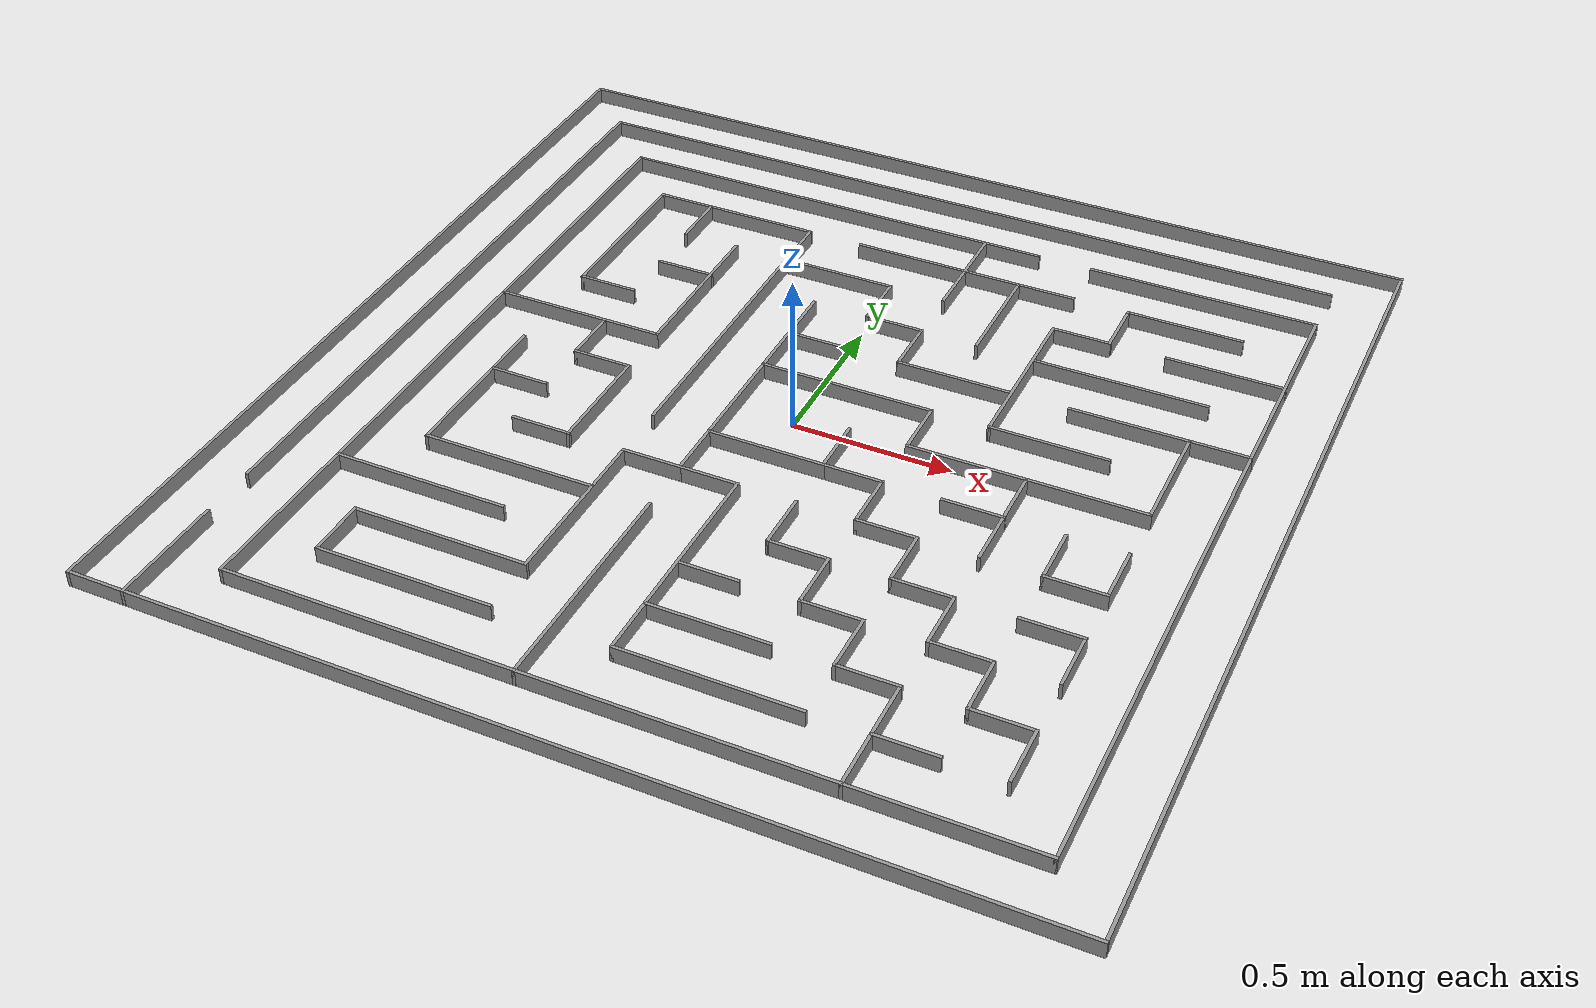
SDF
<?xml version='1.0'?>
<sdf version='1.7'>
  <model name='Maze1'>
    <pose>-0.527918 0 0 0 -0 0</pose>
    <link name='Wall_0'>
      <collision name='Wall_0_Collision'>
        <geometry>
          <box>
            <size>2.89 0.01 0.05</size>
          </box>
        </geometry>
        <pose>0 0 0.025 0 -0 0</pose>
      </collision>
      <visual name='Wall_0_Visual'>
        <pose>0 0 0.025 0 -0 0</pose>
        <geometry>
          <box>
            <size>2.89 0.01 0.05</size>
          </box>
        </geometry>
        <material>
          <script>
            <uri>file://media/materials/scripts/gazebo.material</uri>
            <name>Gazebo/Grey</name>
          </script>
          <ambient>1 1 1 1</ambient>
        </material>
        <meta>
          <layer>0</layer>
        </meta>
      </visual>
      <pose>0.527918 -1.44 0 0 -0 0</pose>
    </link>
    <link name='Wall_11'>
      <collision name='Wall_11_Collision'>
        <geometry>
          <box>
            <size>0.19 0.01 0.05</size>
          </box>
        </geometry>
        <pose>0 0 0.025 0 -0 0</pose>
      </collision>
      <visual name='Wall_11_Visual'>
        <pose>0 0 0.025 0 -0 0</pose>
        <geometry>
          <box>
            <size>0.19 0.01 0.05</size>
          </box>
        </geometry>
        <material>
          <script>
            <uri>file://media/materials/scripts/gazebo.material</uri>
            <name>Gazebo/Grey</name>
          </script>
          <ambient>1 1 1 1</ambient>
        </material>
        <meta>
          <layer>0</layer>
        </meta>
      </visual>
      <pose>0.707918 -0.09 0 0 -0 -1.5708</pose>
    </link>
    <link name='Wall_115'>
      <collision name='Wall_115_Collision'>
        <geometry>
          <box>
            <size>0.19 0.01 0.05</size>
          </box>
        </geometry>
        <pose>0 0 0.025 0 -0 0</pose>
      </collision>
      <visual name='Wall_115_Visual'>
        <pose>0 0 0.025 0 -0 0</pose>
        <geometry>
          <box>
            <size>0.19 0.01 0.05</size>
          </box>
        </geometry>
        <material>
          <script>
            <uri>file://media/materials/scripts/gazebo.material</uri>
            <name>Gazebo/Grey</name>
          </script>
          <ambient>1 1 1 1</ambient>
        </material>
        <meta>
          <layer>0</layer>
        </meta>
      </visual>
      <pose>0.977918 -0.72 0 0 -0 3.14159</pose>
    </link>
    <link name='Wall_116'>
      <collision name='Wall_116_Collision'>
        <geometry>
          <box>
            <size>0.19 0.01 0.05</size>
          </box>
        </geometry>
        <pose>0 0 0.025 0 -0 0</pose>
      </collision>
      <visual name='Wall_116_Visual'>
        <pose>0 0 0.025 0 -0 0</pose>
        <geometry>
          <box>
            <size>0.19 0.01 0.05</size>
          </box>
        </geometry>
        <material>
          <script>
            <uri>file://media/materials/scripts/gazebo.material</uri>
            <name>Gazebo/Grey</name>
          </script>
          <ambient>1 1 1 1</ambient>
        </material>
        <meta>
          <layer>0</layer>
        </meta>
      </visual>
      <pose>0.887918 -0.63 0 0 -0 1.5708</pose>
    </link>
    <link name='Wall_117'>
      <collision name='Wall_117_Collision'>
        <geometry>
          <box>
            <size>0.190641 0.01 0.05</size>
          </box>
        </geometry>
        <pose>0 0 0.025 0 -0 0</pose>
      </collision>
      <visual name='Wall_117_Visual'>
        <pose>0 0 0.025 0 -0 0</pose>
        <geometry>
          <box>
            <size>0.190641 0.01 0.05</size>
          </box>
        </geometry>
        <material>
          <script>
            <uri>file://media/materials/scripts/gazebo.material</uri>
            <name>Gazebo/Grey</name>
          </script>
          <ambient>1 1 1 1</ambient>
        </material>
        <meta>
          <layer>0</layer>
        </meta>
      </visual>
      <pose>0.797918 -0.54 0 0 -0 3.14159</pose>
    </link>
    <link name='Wall_118'>
      <collision name='Wall_118_Collision'>
        <geometry>
          <box>
            <size>0.19 0.01 0.05</size>
          </box>
        </geometry>
        <pose>0 0 0.025 0 -0 0</pose>
      </collision>
      <visual name='Wall_118_Visual'>
        <pose>0 0 0.025 0 -0 0</pose>
        <geometry>
          <box>
            <size>0.19 0.01 0.05</size>
          </box>
        </geometry>
        <material>
          <script>
            <uri>file://media/materials/scripts/gazebo.material</uri>
            <name>Gazebo/Grey</name>
          </script>
          <ambient>1 1 1 1</ambient>
        </material>
        <meta>
          <layer>0</layer>
        </meta>
      </visual>
      <pose>0.707918 -0.45 0 0 -0 1.5708</pose>
    </link>
    <link name='Wall_12'>
      <collision name='Wall_12_Collision'>
        <geometry>
          <box>
            <size>0.37 0.01 0.05</size>
          </box>
        </geometry>
        <pose>0 0 0.025 0 -0 0</pose>
      </collision>
      <visual name='Wall_12_Visual'>
        <pose>0 0 0.025 0 -0 0</pose>
        <geometry>
          <box>
            <size>0.37 0.01 0.05</size>
          </box>
        </geometry>
        <material>
          <script>
            <uri>file://media/materials/scripts/gazebo.material</uri>
            <name>Gazebo/Grey</name>
          </script>
          <ambient>1 1 1 1</ambient>
        </material>
        <meta>
          <layer>0</layer>
        </meta>
      </visual>
      <pose>0.527918 -0.18 0 0 -0 3.14159</pose>
    </link>
    <link name='Wall_120'>
      <collision name='Wall_120_Collision'>
        <geometry>
          <box>
            <size>0.19 0.01 0.05</size>
          </box>
        </geometry>
        <pose>0 0 0.025 0 -0 0</pose>
      </collision>
      <visual name='Wall_120_Visual'>
        <pose>0 0 0.025 0 -0 0</pose>
        <geometry>
          <box>
            <size>0.19 0.01 0.05</size>
          </box>
        </geometry>
        <material>
          <script>
            <uri>file://media/materials/scripts/gazebo.material</uri>
            <name>Gazebo/Grey</name>
          </script>
          <ambient>1 1 1 1</ambient>
        </material>
        <meta>
          <layer>0</layer>
        </meta>
      </visual>
      <pose>0.617918 -0.72 0 0 -0 0</pose>
    </link>
    <link name='Wall_123'>
      <collision name='Wall_123_Collision'>
        <geometry>
          <box>
            <size>0.37 0.01 0.05</size>
          </box>
        </geometry>
        <pose>0 0 0.025 0 -0 0</pose>
      </collision>
      <visual name='Wall_123_Visual'>
        <pose>0 0 0.025 0 -0 0</pose>
        <geometry>
          <box>
            <size>0.37 0.01 0.05</size>
          </box>
        </geometry>
        <material>
          <script>
            <uri>file://media/materials/scripts/gazebo.material</uri>
            <name>Gazebo/Grey</name>
          </script>
          <ambient>1 1 1 1</ambient>
        </material>
        <meta>
          <layer>0</layer>
        </meta>
      </visual>
      <pose>0.707918 -0.9 0 0 -0 0</pose>
    </link>
    <link name='Wall_125'>
      <collision name='Wall_125_Collision'>
        <geometry>
          <box>
            <size>0.55 0.01 0.05</size>
          </box>
        </geometry>
        <pose>0 0 0.025 0 -0 0</pose>
      </collision>
      <visual name='Wall_125_Visual'>
        <pose>0 0 0.025 0 -0 0</pose>
        <geometry>
          <box>
            <size>0.55 0.01 0.05</size>
          </box>
        </geometry>
        <material>
          <script>
            <uri>file://media/materials/scripts/gazebo.material</uri>
            <name>Gazebo/Grey</name>
          </script>
          <ambient>1 1 1 1</ambient>
        </material>
        <meta>
          <layer>0</layer>
        </meta>
      </visual>
      <pose>1.51792 -1.26 0 0 -0 0</pose>
    </link>
    <link name='Wall_126'>
      <collision name='Wall_126_Collision'>
        <geometry>
          <box>
            <size>1.63 0.01 0.05</size>
          </box>
        </geometry>
        <pose>0 0 0.025 0 -0 0</pose>
      </collision>
      <visual name='Wall_126_Visual'>
        <pose>0 0 0.025 0 -0 0</pose>
        <geometry>
          <box>
            <size>1.63 0.01 0.05</size>
          </box>
        </geometry>
        <material>
          <script>
            <uri>file://media/materials/scripts/gazebo.material</uri>
            <name>Gazebo/Grey</name>
          </script>
          <ambient>1 1 1 1</ambient>
        </material>
        <meta>
          <layer>0</layer>
        </meta>
      </visual>
      <pose>1.78792 -0.45 0 0 -0 1.5708</pose>
    </link>
    <link name='Wall_128'>
      <collision name='Wall_128_Collision'>
        <geometry>
          <box>
            <size>0.19 0.01 0.05</size>
          </box>
        </geometry>
        <pose>0 0 0.025 0 -0 0</pose>
      </collision>
      <visual name='Wall_128_Visual'>
        <pose>0 0 0.025 0 -0 0</pose>
        <geometry>
          <box>
            <size>0.19 0.01 0.05</size>
          </box>
        </geometry>
        <material>
          <script>
            <uri>file://media/materials/scripts/gazebo.material</uri>
            <name>Gazebo/Grey</name>
          </script>
          <ambient>1 1 1 1</ambient>
        </material>
        <meta>
          <layer>0</layer>
        </meta>
      </visual>
      <pose>0.257918 -0.36 0 0 -0 3.14159</pose>
    </link>
    <link name='Wall_129'>
      <collision name='Wall_129_Collision'>
        <geometry>
          <box>
            <size>0.55 0.01 0.05</size>
          </box>
        </geometry>
        <pose>0 0 0.025 0 -0 0</pose>
      </collision>
      <visual name='Wall_129_Visual'>
        <pose>0 0 0.025 0 -0 0</pose>
        <geometry>
          <box>
            <size>0.55 0.01 0.05</size>
          </box>
        </geometry>
        <material>
          <script>
            <uri>file://media/materials/scripts/gazebo.material</uri>
            <name>Gazebo/Grey</name>
          </script>
          <ambient>1 1 1 1</ambient>
        </material>
        <meta>
          <layer>0</layer>
        </meta>
      </visual>
      <pose>0.167918 -0.63 0 0 -0 -1.5708</pose>
    </link>
    <link name='Wall_13'>
      <collision name='Wall_13_Collision'>
        <geometry>
          <box>
            <size>0.37 0.01 0.05</size>
          </box>
        </geometry>
        <pose>0 0 0.025 0 -0 0</pose>
      </collision>
      <visual name='Wall_13_Visual'>
        <pose>0 0 0.025 0 -0 0</pose>
        <geometry>
          <box>
            <size>0.37 0.01 0.05</size>
          </box>
        </geometry>
        <material>
          <script>
            <uri>file://media/materials/scripts/gazebo.material</uri>
            <name>Gazebo/Grey</name>
          </script>
          <ambient>1 1 1 1</ambient>
        </material>
        <meta>
          <layer>0</layer>
        </meta>
      </visual>
      <pose>0.347918 0 0 0 -0 1.5708</pose>
    </link>
    <link name='Wall_130'>
      <collision name='Wall_130_Collision'>
        <geometry>
          <box>
            <size>0.55 0.01 0.05</size>
          </box>
        </geometry>
        <pose>0 0 0.025 0 -0 0</pose>
      </collision>
      <visual name='Wall_130_Visual'>
        <pose>0 0 0.025 0 -0 0</pose>
        <geometry>
          <box>
            <size>0.55 0.01 0.05</size>
          </box>
        </geometry>
        <material>
          <script>
            <uri>file://media/materials/scripts/gazebo.material</uri>
            <name>Gazebo/Grey</name>
          </script>
          <ambient>1 1 1 1</ambient>
        </material>
        <meta>
          <layer>0</layer>
        </meta>
      </visual>
      <pose>-0.102082 -0.9 0 0 -0 3.14159</pose>
    </link>
    <link name='Wall_131'>
      <collision name='Wall_131_Collision'>
        <geometry>
          <box>
            <size>0.189303 0.01 0.05</size>
          </box>
        </geometry>
        <pose>0 0 0.025 0 -0 0</pose>
      </collision>
      <visual name='Wall_131_Visual'>
        <pose>0 0 0.025 0 -0 0</pose>
        <geometry>
          <box>
            <size>0.189303 0.01 0.05</size>
          </box>
        </geometry>
        <material>
          <script>
            <uri>file://media/materials/scripts/gazebo.material</uri>
            <name>Gazebo/Grey</name>
          </script>
          <ambient>1 1 1 1</ambient>
        </material>
        <meta>
          <layer>0</layer>
        </meta>
      </visual>
      <pose>-0.372082 -0.99 0 0 -0 -1.5708</pose>
    </link>
    <link name='Wall_132'>
      <collision name='Wall_132_Collision'>
        <geometry>
          <box>
            <size>0.55 0.01 0.05</size>
          </box>
        </geometry>
        <pose>0 0 0.025 0 -0 0</pose>
      </collision>
      <visual name='Wall_132_Visual'>
        <pose>0 0 0.025 0 -0 0</pose>
        <geometry>
          <box>
            <size>0.55 0.01 0.05</size>
          </box>
        </geometry>
        <material>
          <script>
            <uri>file://media/materials/scripts/gazebo.material</uri>
            <name>Gazebo/Grey</name>
          </script>
          <ambient>1 1 1 1</ambient>
        </material>
        <meta>
          <layer>0</layer>
        </meta>
      </visual>
      <pose>-0.102082 -1.08 0 0 -0 0</pose>
    </link>
    <link name='Wall_135'>
      <collision name='Wall_135_Collision'>
        <geometry>
          <box>
            <size>0.19 0.01 0.05</size>
          </box>
        </geometry>
        <pose>0 0 0.025 0 -0 0</pose>
      </collision>
      <visual name='Wall_135_Visual'>
        <pose>0 0 0.025 0 -0 0</pose>
        <geometry>
          <box>
            <size>0.19 0.01 0.05</size>
          </box>
        </geometry>
        <material>
          <script>
            <uri>file://media/materials/scripts/gazebo.material</uri>
            <name>Gazebo/Grey</name>
          </script>
          <ambient>1 1 1 1</ambient>
        </material>
        <meta>
          <layer>0</layer>
        </meta>
      </visual>
      <pose>1.51792 -0.54 0 0 -0 0</pose>
    </link>
    <link name='Wall_136'>
      <collision name='Wall_136_Collision'>
        <geometry>
          <box>
            <size>0.19 0.01 0.05</size>
          </box>
        </geometry>
        <pose>0 0 0.025 0 -0 0</pose>
      </collision>
      <visual name='Wall_136_Visual'>
        <pose>0 0 0.025 0 -0 0</pose>
        <geometry>
          <box>
            <size>0.19 0.01 0.05</size>
          </box>
        </geometry>
        <material>
          <script>
            <uri>file://media/materials/scripts/gazebo.material</uri>
            <name>Gazebo/Grey</name>
          </script>
          <ambient>1 1 1 1</ambient>
        </material>
        <meta>
          <layer>0</layer>
        </meta>
      </visual>
      <pose>1.60792 -0.63 0 0 -0 -1.5708</pose>
    </link>
    <link name='Wall_138'>
      <collision name='Wall_138_Collision'>
        <geometry>
          <box>
            <size>0.19 0.01 0.05</size>
          </box>
        </geometry>
        <pose>0 0 0.025 0 -0 0</pose>
      </collision>
      <visual name='Wall_138_Visual'>
        <pose>0 0 0.025 0 -0 0</pose>
        <geometry>
          <box>
            <size>0.19 0.01 0.05</size>
          </box>
        </geometry>
        <material>
          <script>
            <uri>file://media/materials/scripts/gazebo.material</uri>
            <name>Gazebo/Grey</name>
          </script>
          <ambient>1 1 1 1</ambient>
        </material>
        <meta>
          <layer>0</layer>
        </meta>
      </visual>
      <pose>1.42792 -0.27 0 0 -0 -1.5708</pose>
    </link>
    <link name='Wall_139'>
      <collision name='Wall_139_Collision'>
        <geometry>
          <box>
            <size>0.19 0.01 0.05</size>
          </box>
        </geometry>
        <pose>0 0 0.025 0 -0 0</pose>
      </collision>
      <visual name='Wall_139_Visual'>
        <pose>0 0 0.025 0 -0 0</pose>
        <geometry>
          <box>
            <size>0.19 0.01 0.05</size>
          </box>
        </geometry>
        <material>
          <script>
            <uri>file://media/materials/scripts/gazebo.material</uri>
            <name>Gazebo/Grey</name>
          </script>
          <ambient>1 1 1 1</ambient>
        </material>
        <meta>
          <layer>0</layer>
        </meta>
      </visual>
      <pose>1.51792 -0.36 0 0 -0 0</pose>
    </link>
    <link name='Wall_14'>
      <collision name='Wall_14_Collision'>
        <geometry>
          <box>
            <size>0.55 0.01 0.05</size>
          </box>
        </geometry>
        <pose>0 0 0.025 0 -0 0</pose>
      </collision>
      <visual name='Wall_14_Visual'>
        <pose>0 0 0.025 0 -0 0</pose>
        <geometry>
          <box>
            <size>0.55 0.01 0.05</size>
          </box>
        </geometry>
        <material>
          <script>
            <uri>file://media/materials/scripts/gazebo.material</uri>
            <name>Gazebo/Grey</name>
          </script>
          <ambient>1 1 1 1</ambient>
        </material>
        <meta>
          <layer>0</layer>
        </meta>
      </visual>
      <pose>0.617918 0.18 0 0 -0 0</pose>
    </link>
    <link name='Wall_140'>
      <collision name='Wall_140_Collision'>
        <geometry>
          <box>
            <size>0.19 0.01 0.05</size>
          </box>
        </geometry>
        <pose>0 0 0.025 0 -0 0</pose>
      </collision>
      <visual name='Wall_140_Visual'>
        <pose>0 0 0.025 0 -0 0</pose>
        <geometry>
          <box>
            <size>0.19 0.01 0.05</size>
          </box>
        </geometry>
        <material>
          <script>
            <uri>file://media/materials/scripts/gazebo.material</uri>
            <name>Gazebo/Grey</name>
          </script>
          <ambient>1 1 1 1</ambient>
        </material>
        <meta>
          <layer>0</layer>
        </meta>
      </visual>
      <pose>1.60792 -0.27 0 0 -0 1.5708</pose>
    </link>
    <link name='Wall_142'>
      <collision name='Wall_142_Collision'>
        <geometry>
          <box>
            <size>0.37 0.01 0.05</size>
          </box>
        </geometry>
        <pose>0 0 0.025 0 -0 0</pose>
      </collision>
      <visual name='Wall_142_Visual'>
        <pose>0 0 0.025 0 -0 0</pose>
        <geometry>
          <box>
            <size>0.37 0.01 0.05</size>
          </box>
        </geometry>
        <material>
          <script>
            <uri>file://media/materials/scripts/gazebo.material</uri>
            <name>Gazebo/Grey</name>
          </script>
          <ambient>1 1 1 1</ambient>
        </material>
        <meta>
          <layer>0</layer>
        </meta>
      </visual>
      <pose>1.24792 -0.18 0 0 -0 -1.5708</pose>
    </link>
    <link name='Wall_144'>
      <collision name='Wall_144_Collision'>
        <geometry>
          <box>
            <size>0.19 0.01 0.05</size>
          </box>
        </geometry>
        <pose>0 0 0.025 0 -0 0</pose>
      </collision>
      <visual name='Wall_144_Visual'>
        <pose>0 0 0.025 0 -0 0</pose>
        <geometry>
          <box>
            <size>0.19 0.01 0.05</size>
          </box>
        </geometry>
        <material>
          <script>
            <uri>file://media/materials/scripts/gazebo.material</uri>
            <name>Gazebo/Grey</name>
          </script>
          <ambient>1 1 1 1</ambient>
        </material>
        <meta>
          <layer>0</layer>
        </meta>
      </visual>
      <pose>1.15792 -0.18 0 0 -0 3.14159</pose>
    </link>
    <link name='Wall_147'>
      <collision name='Wall_147_Collision'>
        <geometry>
          <box>
            <size>0.55 0.01 0.05</size>
          </box>
        </geometry>
        <pose>0 0 0.025 0 -0 0</pose>
      </collision>
      <visual name='Wall_147_Visual'>
        <pose>0 0 0.025 0 -0 0</pose>
        <geometry>
          <box>
            <size>0.55 0.01 0.05</size>
          </box>
        </geometry>
        <material>
          <script>
            <uri>file://media/materials/scripts/gazebo.material</uri>
            <name>Gazebo/Grey</name>
          </script>
          <ambient>1 1 1 1</ambient>
        </material>
        <meta>
          <layer>0</layer>
        </meta>
      </visual>
      <pose>-0.102082 -0.54 0 0 -0 3.14159</pose>
    </link>
    <link name='Wall_148'>
      <collision name='Wall_148_Collision'>
        <geometry>
          <box>
            <size>0.55 0.01 0.05</size>
          </box>
        </geometry>
        <pose>0 0 0.025 0 -0 0</pose>
      </collision>
      <visual name='Wall_148_Visual'>
        <pose>0 0 0.025 0 -0 0</pose>
        <geometry>
          <box>
            <size>0.55 0.01 0.05</size>
          </box>
        </geometry>
        <material>
          <script>
            <uri>file://media/materials/scripts/gazebo.material</uri>
            <name>Gazebo/Grey</name>
          </script>
          <ambient>1 1 1 1</ambient>
        </material>
        <meta>
          <layer>0</layer>
        </meta>
      </visual>
      <pose>-0.372082 -0.27 0 0 -0 1.5708</pose>
    </link>
    <link name='Wall_15'>
      <collision name='Wall_15_Collision'>
        <geometry>
          <box>
            <size>0.19 0.01 0.05</size>
          </box>
        </geometry>
        <pose>0 0 0.025 0 -0 0</pose>
      </collision>
      <visual name='Wall_15_Visual'>
        <pose>0 0 0.025 0 -0 0</pose>
        <geometry>
          <box>
            <size>0.19 0.01 0.05</size>
          </box>
        </geometry>
        <material>
          <script>
            <uri>file://media/materials/scripts/gazebo.material</uri>
            <name>Gazebo/Grey</name>
          </script>
          <ambient>1 1 1 1</ambient>
        </material>
        <meta>
          <layer>0</layer>
        </meta>
      </visual>
      <pose>0.887918 0.09 0 0 -0 -1.5708</pose>
    </link>
    <link name='Wall_151'>
      <collision name='Wall_151_Collision'>
        <geometry>
          <box>
            <size>0.19 0.01 0.05</size>
          </box>
        </geometry>
        <pose>0 0 0.025 0 -0 0</pose>
      </collision>
      <visual name='Wall_151_Visual'>
        <pose>0 0 0.025 0 -0 0</pose>
        <geometry>
          <box>
            <size>0.19 0.01 0.05</size>
          </box>
        </geometry>
        <material>
          <script>
            <uri>file://media/materials/scripts/gazebo.material</uri>
            <name>Gazebo/Grey</name>
          </script>
          <ambient>1 1 1 1</ambient>
        </material>
        <meta>
          <layer>0</layer>
        </meta>
      </visual>
      <pose>-0.282082 -0.18 0 0 -0 0</pose>
    </link>
    <link name='Wall_153'>
      <collision name='Wall_153_Collision'>
        <geometry>
          <box>
            <size>0.73 0.01 0.05</size>
          </box>
        </geometry>
        <pose>0 0 0.025 0 -0 0</pose>
      </collision>
      <visual name='Wall_153_Visual'>
        <pose>0 0 0.025 0 -0 0</pose>
        <geometry>
          <box>
            <size>0.73 0.01 0.05</size>
          </box>
        </geometry>
        <material>
          <script>
            <uri>file://media/materials/scripts/gazebo.material</uri>
            <name>Gazebo/Grey</name>
          </script>
          <ambient>1 1 1 1</ambient>
        </material>
        <meta>
          <layer>0</layer>
        </meta>
      </visual>
      <pose>1.78792 0.72 0 0 -0 1.5708</pose>
    </link>
    <link name='Wall_154'>
      <collision name='Wall_154_Collision'>
        <geometry>
          <box>
            <size>0.73 0.01 0.05</size>
          </box>
        </geometry>
        <pose>0 0 0.025 0 -0 0</pose>
      </collision>
      <visual name='Wall_154_Visual'>
        <pose>0 0 0.025 0 -0 0</pose>
        <geometry>
          <box>
            <size>0.73 0.01 0.05</size>
          </box>
        </geometry>
        <material>
          <script>
            <uri>file://media/materials/scripts/gazebo.material</uri>
            <name>Gazebo/Grey</name>
          </script>
          <ambient>1 1 1 1</ambient>
        </material>
        <meta>
          <layer>0</layer>
        </meta>
      </visual>
      <pose>1.42792 1.08 0 0 -0 3.14159</pose>
    </link>
    <link name='Wall_156'>
      <collision name='Wall_156_Collision'>
        <geometry>
          <box>
            <size>0.37 0.01 0.05</size>
          </box>
        </geometry>
        <pose>0 0 0.025 0 -0 0</pose>
      </collision>
      <visual name='Wall_156_Visual'>
        <pose>0 0 0.025 0 -0 0</pose>
        <geometry>
          <box>
            <size>0.37 0.01 0.05</size>
          </box>
        </geometry>
        <material>
          <script>
            <uri>file://media/materials/scripts/gazebo.material</uri>
            <name>Gazebo/Grey</name>
          </script>
          <ambient>1 1 1 1</ambient>
        </material>
        <meta>
          <layer>0</layer>
        </meta>
      </visual>
      <pose>1.60792 0.72 0 0 -0 3.14159</pose>
    </link>
    <link name='Wall_158'>
      <collision name='Wall_158_Collision'>
        <geometry>
          <box>
            <size>0.37 0.01 0.05</size>
          </box>
        </geometry>
        <pose>0 0 0.025 0 -0 0</pose>
      </collision>
      <visual name='Wall_158_Visual'>
        <pose>0 0 0.025 0 -0 0</pose>
        <geometry>
          <box>
            <size>0.37 0.01 0.05</size>
          </box>
        </geometry>
        <material>
          <script>
            <uri>file://media/materials/scripts/gazebo.material</uri>
            <name>Gazebo/Grey</name>
          </script>
          <ambient>1 1 1 1</ambient>
        </material>
        <meta>
          <layer>0</layer>
        </meta>
      </visual>
      <pose>0.347918 0.36 0 0 -0 1.5708</pose>
    </link>
    <link name='Wall_16'>
      <collision name='Wall_16_Collision'>
        <geometry>
          <box>
            <size>0.73 0.01 0.05</size>
          </box>
        </geometry>
        <pose>0 0 0.025 0 -0 0</pose>
      </collision>
      <visual name='Wall_16_Visual'>
        <pose>0 0 0.025 0 -0 0</pose>
        <geometry>
          <box>
            <size>0.73 0.01 0.05</size>
          </box>
        </geometry>
        <material>
          <script>
            <uri>file://media/materials/scripts/gazebo.material</uri>
            <name>Gazebo/Grey</name>
          </script>
          <ambient>1 1 1 1</ambient>
        </material>
        <meta>
          <layer>0</layer>
        </meta>
      </visual>
      <pose>1.24792 0 0 0 -0 0</pose>
    </link>
    <link name='Wall_160'>
      <collision name='Wall_160_Collision'>
        <geometry>
          <box>
            <size>0.19 0.01 0.05</size>
          </box>
        </geometry>
        <pose>0 0 0.025 0 -0 0</pose>
      </collision>
      <visual name='Wall_160_Visual'>
        <pose>0 0 0.025 0 -0 0</pose>
        <geometry>
          <box>
            <size>0.19 0.01 0.05</size>
          </box>
        </geometry>
        <material>
          <script>
            <uri>file://media/materials/scripts/gazebo.material</uri>
            <name>Gazebo/Grey</name>
          </script>
          <ambient>1 1 1 1</ambient>
        </material>
        <meta>
          <layer>0</layer>
        </meta>
      </visual>
      <pose>0.437918 0.36 0 0 -0 0</pose>
    </link>
    <link name='Wall_162'>
      <collision name='Wall_162_Collision'>
        <geometry>
          <box>
            <size>0.91 0.01 0.05</size>
          </box>
        </geometry>
        <pose>0 0 0.025 0 -0 0</pose>
      </collision>
      <visual name='Wall_162_Visual'>
        <pose>0 0 0.025 0 -0 0</pose>
        <geometry>
          <box>
            <size>0.91 0.01 0.05</size>
          </box>
        </geometry>
        <material>
          <script>
            <uri>file://media/materials/scripts/gazebo.material</uri>
            <name>Gazebo/Grey</name>
          </script>
          <ambient>1 1 1 1</ambient>
        </material>
        <meta>
          <layer>0</layer>
        </meta>
      </visual>
      <pose>-0.552082 -0.27 0 0 -0 1.5708</pose>
    </link>
    <link name='Wall_163'>
      <collision name='Wall_163_Collision'>
        <geometry>
          <box>
            <size>0.37 0.01 0.05</size>
          </box>
        </geometry>
        <pose>0 0 0.025 0 -0 0</pose>
      </collision>
      <visual name='Wall_163_Visual'>
        <pose>0 0 0.025 0 -0 0</pose>
        <geometry>
          <box>
            <size>0.37 0.01 0.05</size>
          </box>
        </geometry>
        <material>
          <script>
            <uri>file://media/materials/scripts/gazebo.material</uri>
            <name>Gazebo/Grey</name>
          </script>
          <ambient>1 1 1 1</ambient>
        </material>
        <meta>
          <layer>0</layer>
        </meta>
      </visual>
      <pose>-0.372082 0.18 0 0 -0 0</pose>
    </link>
    <link name='Wall_164'>
      <collision name='Wall_164_Collision'>
        <geometry>
          <box>
            <size>0.19 0.01 0.05</size>
          </box>
        </geometry>
        <pose>0 0 0.025 0 -0 0</pose>
      </collision>
      <visual name='Wall_164_Visual'>
        <pose>0 0 0.025 0 -0 0</pose>
        <geometry>
          <box>
            <size>0.19 0.01 0.05</size>
          </box>
        </geometry>
        <material>
          <script>
            <uri>file://media/materials/scripts/gazebo.material</uri>
            <name>Gazebo/Grey</name>
          </script>
          <ambient>1 1 1 1</ambient>
        </material>
        <meta>
          <layer>0</layer>
        </meta>
      </visual>
      <pose>-0.192082 0.09 0 0 -0 -1.5708</pose>
    </link>
    <link name='Wall_165'>
      <collision name='Wall_165_Collision'>
        <geometry>
          <box>
            <size>0.19 0.01 0.05</size>
          </box>
        </geometry>
        <pose>0 0 0.025 0 -0 0</pose>
      </collision>
      <visual name='Wall_165_Visual'>
        <pose>0 0 0.025 0 -0 0</pose>
        <geometry>
          <box>
            <size>0.19 0.01 0.05</size>
          </box>
        </geometry>
        <material>
          <script>
            <uri>file://media/materials/scripts/gazebo.material</uri>
            <name>Gazebo/Grey</name>
          </script>
          <ambient>1 1 1 1</ambient>
        </material>
        <meta>
          <layer>0</layer>
        </meta>
      </visual>
      <pose>-0.102082 0 0 0 -0 0</pose>
    </link>
    <link name='Wall_169'>
      <collision name='Wall_169_Collision'>
        <geometry>
          <box>
            <size>0.91 0.01 0.05</size>
          </box>
        </geometry>
        <pose>0 0 0.025 0 -0 0</pose>
      </collision>
      <visual name='Wall_169_Visual'>
        <pose>0 0 0.025 0 -0 0</pose>
        <geometry>
          <box>
            <size>0.91 0.01 0.05</size>
          </box>
        </geometry>
        <material>
          <script>
            <uri>file://media/materials/scripts/gazebo.material</uri>
            <name>Gazebo/Grey</name>
          </script>
          <ambient>1 1 1 1</ambient>
        </material>
        <meta>
          <layer>0</layer>
        </meta>
      </visual>
      <pose>-0.552082 0.63 0 0 -0 1.5708</pose>
    </link>
    <link name='Wall_17'>
      <collision name='Wall_17_Collision'>
        <geometry>
          <box>
            <size>0.37 0.01 0.05</size>
          </box>
        </geometry>
        <pose>0 0 0.025 0 -0 0</pose>
      </collision>
      <visual name='Wall_17_Visual'>
        <pose>0 0 0.025 0 -0 0</pose>
        <geometry>
          <box>
            <size>0.37 0.01 0.05</size>
          </box>
        </geometry>
        <material>
          <script>
            <uri>file://media/materials/scripts/gazebo.material</uri>
            <name>Gazebo/Grey</name>
          </script>
          <ambient>1 1 1 1</ambient>
        </material>
        <meta>
          <layer>0</layer>
        </meta>
      </visual>
      <pose>1.60792 0.18 0 0 -0 1.5708</pose>
    </link>
    <link name='Wall_170'>
      <collision name='Wall_170_Collision'>
        <geometry>
          <box>
            <size>1.45 0.01 0.05</size>
          </box>
        </geometry>
        <pose>0 0 0.025 0 -0 0</pose>
      </collision>
      <visual name='Wall_170_Visual'>
        <pose>0 0 0.025 0 -0 0</pose>
        <geometry>
          <box>
            <size>1.45 0.01 0.05</size>
          </box>
        </geometry>
        <material>
          <script>
            <uri>file://media/materials/scripts/gazebo.material</uri>
            <name>Gazebo/Grey</name>
          </script>
          <ambient>1 1 1 1</ambient>
        </material>
        <meta>
          <layer>0</layer>
        </meta>
      </visual>
      <pose>0.167918 1.08 0 0 -0 0</pose>
    </link>
    <link name='Wall_179'>
      <collision name='Wall_179_Collision'>
        <geometry>
          <box>
            <size>0.370044 0.01 0.05</size>
          </box>
        </geometry>
        <pose>0 0 0.025 0 -0 0</pose>
      </collision>
      <visual name='Wall_179_Visual'>
        <pose>0 0 0.025 0 -0 0</pose>
        <geometry>
          <box>
            <size>0.370044 0.01 0.05</size>
          </box>
        </geometry>
        <material>
          <script>
            <uri>file://media/materials/scripts/gazebo.material</uri>
            <name>Gazebo/Grey</name>
          </script>
          <ambient>1 1 1 1</ambient>
        </material>
        <meta>
          <layer>0</layer>
        </meta>
      </visual>
      <pose>-0.012082 -0.18 0 0 -0 -1.5708</pose>
    </link>
    <link name='Wall_18'>
      <collision name='Wall_18_Collision'>
        <geometry>
          <box>
            <size>0.19 0.01 0.05</size>
          </box>
        </geometry>
        <pose>0 0 0.025 0 -0 0</pose>
      </collision>
      <visual name='Wall_18_Visual'>
        <pose>0 0 0.025 0 -0 0</pose>
        <geometry>
          <box>
            <size>0.19 0.01 0.05</size>
          </box>
        </geometry>
        <material>
          <script>
            <uri>file://media/materials/scripts/gazebo.material</uri>
            <name>Gazebo/Grey</name>
          </script>
          <ambient>1 1 1 1</ambient>
        </material>
        <meta>
          <layer>0</layer>
        </meta>
      </visual>
      <pose>1.69792 0.36 0 0 -0 0</pose>
    </link>
    <link name='Wall_180'>
      <collision name='Wall_180_Collision'>
        <geometry>
          <box>
            <size>0.19 0.01 0.05</size>
          </box>
        </geometry>
        <pose>0 0 0.025 0 -0 0</pose>
      </collision>
      <visual name='Wall_180_Visual'>
        <pose>0 0 0.025 0 -0 0</pose>
        <geometry>
          <box>
            <size>0.19 0.01 0.05</size>
          </box>
        </geometry>
        <material>
          <script>
            <uri>file://media/materials/scripts/gazebo.material</uri>
            <name>Gazebo/Grey</name>
          </script>
          <ambient>1 1 1 1</ambient>
        </material>
        <meta>
          <layer>0</layer>
        </meta>
      </visual>
      <pose>-0.102082 -0.36 0 0 -0 3.14159</pose>
    </link>
    <link name='Wall_186'>
      <collision name='Wall_186_Collision'>
        <geometry>
          <box>
            <size>0.19 0.01 0.05</size>
          </box>
        </geometry>
        <pose>0 0 0.025 0 -0 0</pose>
      </collision>
      <visual name='Wall_186_Visual'>
        <pose>0 0 0.025 0 -0 0</pose>
        <geometry>
          <box>
            <size>0.19 0.01 0.05</size>
          </box>
        </geometry>
        <material>
          <script>
            <uri>file://media/materials/scripts/gazebo.material</uri>
            <name>Gazebo/Grey</name>
          </script>
          <ambient>1 1 1 1</ambient>
        </material>
        <meta>
          <layer>0</layer>
        </meta>
      </visual>
      <pose>-0.102082 0.18 0 0 -0 0</pose>
    </link>
    <link name='Wall_187'>
      <collision name='Wall_187_Collision'>
        <geometry>
          <box>
            <size>0.55 0.01 0.05</size>
          </box>
        </geometry>
        <pose>0 0 0.025 0 -0 0</pose>
      </collision>
      <visual name='Wall_187_Visual'>
        <pose>0 0 0.025 0 -0 0</pose>
        <geometry>
          <box>
            <size>0.55 0.01 0.05</size>
          </box>
        </geometry>
        <material>
          <script>
            <uri>file://media/materials/scripts/gazebo.material</uri>
            <name>Gazebo/Grey</name>
          </script>
          <ambient>1 1 1 1</ambient>
        </material>
        <meta>
          <layer>0</layer>
        </meta>
      </visual>
      <pose>-0.012082 0.45 0 0 -0 1.5708</pose>
    </link>
    <link name='Wall_190'>
      <collision name='Wall_190_Collision'>
        <geometry>
          <box>
            <size>0.19 0.01 0.05</size>
          </box>
        </geometry>
        <pose>0 0 0.025 0 -0 0</pose>
      </collision>
      <visual name='Wall_190_Visual'>
        <pose>0 0 0.025 0 -0 0</pose>
        <geometry>
          <box>
            <size>0.19 0.01 0.05</size>
          </box>
        </geometry>
        <material>
          <script>
            <uri>file://media/materials/scripts/gazebo.material</uri>
            <name>Gazebo/Grey</name>
          </script>
          <ambient>1 1 1 1</ambient>
        </material>
        <meta>
          <layer>0</layer>
        </meta>
      </visual>
      <pose>-0.102082 0.54 0 0 -0 3.14159</pose>
    </link>
    <link name='Wall_192'>
      <collision name='Wall_192_Collision'>
        <geometry>
          <box>
            <size>1.09 0.01 0.05</size>
          </box>
        </geometry>
        <pose>0 0 0.025 0 -0 0</pose>
      </collision>
      <visual name='Wall_192_Visual'>
        <pose>0 0 0.025 0 -0 0</pose>
        <geometry>
          <box>
            <size>1.09 0.01 0.05</size>
          </box>
        </geometry>
        <material>
          <script>
            <uri>file://media/materials/scripts/gazebo.material</uri>
            <name>Gazebo/Grey</name>
          </script>
          <ambient>1 1 1 1</ambient>
        </material>
        <meta>
          <layer>0</layer>
        </meta>
      </visual>
      <pose>0.167918 0.36 0 0 -0 1.5708</pose>
    </link>
    <link name='Wall_193'>
      <collision name='Wall_193_Collision'>
        <geometry>
          <box>
            <size>0.55 0.01 0.05</size>
          </box>
        </geometry>
        <pose>0 0 0.025 0 -0 0</pose>
      </collision>
      <visual name='Wall_193_Visual'>
        <pose>0 0 0.025 0 -0 0</pose>
        <geometry>
          <box>
            <size>0.55 0.01 0.05</size>
          </box>
        </geometry>
        <material>
          <script>
            <uri>file://media/materials/scripts/gazebo.material</uri>
            <name>Gazebo/Grey</name>
          </script>
          <ambient>1 1 1 1</ambient>
        </material>
        <meta>
          <layer>0</layer>
        </meta>
      </visual>
      <pose>-0.102082 0.9 0 0 -0 3.14159</pose>
    </link>
    <link name='Wall_194'>
      <collision name='Wall_194_Collision'>
        <geometry>
          <box>
            <size>0.55 0.01 0.05</size>
          </box>
        </geometry>
        <pose>0 0 0.025 0 -0 0</pose>
      </collision>
      <visual name='Wall_194_Visual'>
        <pose>0 0 0.025 0 -0 0</pose>
        <geometry>
          <box>
            <size>0.55 0.01 0.05</size>
          </box>
        </geometry>
        <material>
          <script>
            <uri>file://media/materials/scripts/gazebo.material</uri>
            <name>Gazebo/Grey</name>
          </script>
          <ambient>1 1 1 1</ambient>
        </material>
        <meta>
          <layer>0</layer>
        </meta>
      </visual>
      <pose>-0.372082 0.63 0 0 -0 -1.5708</pose>
    </link>
    <link name='Wall_195'>
      <collision name='Wall_195_Collision'>
        <geometry>
          <box>
            <size>0.19 0.01 0.05</size>
          </box>
        </geometry>
        <pose>0 0 0.025 0 -0 0</pose>
      </collision>
      <visual name='Wall_195_Visual'>
        <pose>0 0 0.025 0 -0 0</pose>
        <geometry>
          <box>
            <size>0.19 0.01 0.05</size>
          </box>
        </geometry>
        <material>
          <script>
            <uri>file://media/materials/scripts/gazebo.material</uri>
            <name>Gazebo/Grey</name>
          </script>
          <ambient>1 1 1 1</ambient>
        </material>
        <meta>
          <layer>0</layer>
        </meta>
      </visual>
      <pose>-0.282082 0.36 0 0 -0 0</pose>
    </link>
    <link name='Wall_197'>
      <collision name='Wall_197_Collision'>
        <geometry>
          <box>
            <size>0.19 0.01 0.05</size>
          </box>
        </geometry>
        <pose>0 0 0.025 0 -0 0</pose>
      </collision>
      <visual name='Wall_197_Visual'>
        <pose>0 0 0.025 0 -0 0</pose>
        <geometry>
          <box>
            <size>0.19 0.01 0.05</size>
          </box>
        </geometry>
        <material>
          <script>
            <uri>file://media/materials/scripts/gazebo.material</uri>
            <name>Gazebo/Grey</name>
          </script>
          <ambient>1 1 1 1</ambient>
        </material>
        <meta>
          <layer>0</layer>
        </meta>
      </visual>
      <pose>-0.192082 0.81 0 0 -0 -1.5708</pose>
    </link>
    <link name='Wall_199'>
      <collision name='Wall_199_Collision'>
        <geometry>
          <box>
            <size>0.37 0.01 0.05</size>
          </box>
        </geometry>
        <pose>0 0 0.025 0 -0 0</pose>
      </collision>
      <visual name='Wall_199_Visual'>
        <pose>0 0 0.025 0 -0 0</pose>
        <geometry>
          <box>
            <size>0.37 0.01 0.05</size>
          </box>
        </geometry>
        <material>
          <script>
            <uri>file://media/materials/scripts/gazebo.material</uri>
            <name>Gazebo/Grey</name>
          </script>
          <ambient>1 1 1 1</ambient>
        </material>
        <meta>
          <layer>0</layer>
        </meta>
      </visual>
      <pose>1.42792 0.9 0 0 -0 3.14159</pose>
    </link>
    <link name='Wall_200'>
      <collision name='Wall_200_Collision'>
        <geometry>
          <box>
            <size>0.19 0.01 0.05</size>
          </box>
        </geometry>
        <pose>0 0 0.025 0 -0 0</pose>
      </collision>
      <visual name='Wall_200_Visual'>
        <pose>0 0 0.025 0 -0 0</pose>
        <geometry>
          <box>
            <size>0.19 0.01 0.05</size>
          </box>
        </geometry>
        <material>
          <script>
            <uri>file://media/materials/scripts/gazebo.material</uri>
            <name>Gazebo/Grey</name>
          </script>
          <ambient>1 1 1 1</ambient>
        </material>
        <meta>
          <layer>0</layer>
        </meta>
      </visual>
      <pose>1.24792 0.81 0 0 -0 -1.5708</pose>
    </link>
    <link name='Wall_201'>
      <collision name='Wall_201_Collision'>
        <geometry>
          <box>
            <size>0.19 0.01 0.05</size>
          </box>
        </geometry>
        <pose>0 0 0.025 0 -0 0</pose>
      </collision>
      <visual name='Wall_201_Visual'>
        <pose>0 0 0.025 0 -0 0</pose>
        <geometry>
          <box>
            <size>0.19 0.01 0.05</size>
          </box>
        </geometry>
        <material>
          <script>
            <uri>file://media/materials/scripts/gazebo.material</uri>
            <name>Gazebo/Grey</name>
          </script>
          <ambient>1 1 1 1</ambient>
        </material>
        <meta>
          <layer>0</layer>
        </meta>
      </visual>
      <pose>1.15792 0.72 0 0 -0 3.14159</pose>
    </link>
    <link name='Wall_202'>
      <collision name='Wall_202_Collision'>
        <geometry>
          <box>
            <size>0.55 0.01 0.05</size>
          </box>
        </geometry>
        <pose>0 0 0.025 0 -0 0</pose>
      </collision>
      <visual name='Wall_202_Visual'>
        <pose>0 0 0.025 0 -0 0</pose>
        <geometry>
          <box>
            <size>0.55 0.01 0.05</size>
          </box>
        </geometry>
        <material>
          <script>
            <uri>file://media/materials/scripts/gazebo.material</uri>
            <name>Gazebo/Grey</name>
          </script>
          <ambient>1 1 1 1</ambient>
        </material>
        <meta>
          <layer>0</layer>
        </meta>
      </visual>
      <pose>1.06792 0.45 0 0 -0 -1.5708</pose>
    </link>
    <link name='Wall_203'>
      <collision name='Wall_203_Collision'>
        <geometry>
          <box>
            <size>0.370972 0.01 0.05</size>
          </box>
        </geometry>
        <pose>0 0 0.025 0 -0 0</pose>
      </collision>
      <visual name='Wall_203_Visual'>
        <pose>0 0 0.025 0 -0 0</pose>
        <geometry>
          <box>
            <size>0.370972 0.01 0.05</size>
          </box>
        </geometry>
        <material>
          <script>
            <uri>file://media/materials/scripts/gazebo.material</uri>
            <name>Gazebo/Grey</name>
          </script>
          <ambient>1 1 1 1</ambient>
        </material>
        <meta>
          <layer>0</layer>
        </meta>
      </visual>
      <pose>1.24792 0.18 0 0 -0 0</pose>
    </link>
    <link name='Wall_206'>
      <collision name='Wall_206_Collision'>
        <geometry>
          <box>
            <size>0.37 0.01 0.05</size>
          </box>
        </geometry>
        <pose>0 0 0.025 0 -0 0</pose>
      </collision>
      <visual name='Wall_206_Visual'>
        <pose>0 0 0.025 0 -0 0</pose>
        <geometry>
          <box>
            <size>0.37 0.01 0.05</size>
          </box>
        </geometry>
        <material>
          <script>
            <uri>file://media/materials/scripts/gazebo.material</uri>
            <name>Gazebo/Grey</name>
          </script>
          <ambient>1 1 1 1</ambient>
        </material>
        <meta>
          <layer>0</layer>
        </meta>
      </visual>
      <pose>0.347918 0.72 0 0 -0 0</pose>
    </link>
    <link name='Wall_207'>
      <collision name='Wall_207_Collision'>
        <geometry>
          <box>
            <size>0.19 0.01 0.05</size>
          </box>
        </geometry>
        <pose>0 0 0.025 0 -0 0</pose>
      </collision>
      <visual name='Wall_207_Visual'>
        <pose>0 0 0.025 0 -0 0</pose>
        <geometry>
          <box>
            <size>0.19 0.01 0.05</size>
          </box>
        </geometry>
        <material>
          <script>
            <uri>file://media/materials/scripts/gazebo.material</uri>
            <name>Gazebo/Grey</name>
          </script>
          <ambient>1 1 1 1</ambient>
        </material>
        <meta>
          <layer>0</layer>
        </meta>
      </visual>
      <pose>0.527918 0.63 0 0 -0 -1.5708</pose>
    </link>
    <link name='Wall_208'>
      <collision name='Wall_208_Collision'>
        <geometry>
          <box>
            <size>0.19 0.01 0.05</size>
          </box>
        </geometry>
        <pose>0 0 0.025 0 -0 0</pose>
      </collision>
      <visual name='Wall_208_Visual'>
        <pose>0 0 0.025 0 -0 0</pose>
        <geometry>
          <box>
            <size>0.19 0.01 0.05</size>
          </box>
        </geometry>
        <material>
          <script>
            <uri>file://media/materials/scripts/gazebo.material</uri>
            <name>Gazebo/Grey</name>
          </script>
          <ambient>1 1 1 1</ambient>
        </material>
        <meta>
          <layer>0</layer>
        </meta>
      </visual>
      <pose>0.617918 0.54 0 0 -0 0</pose>
    </link>
    <link name='Wall_209'>
      <collision name='Wall_209_Collision'>
        <geometry>
          <box>
            <size>0.19 0.01 0.05</size>
          </box>
        </geometry>
        <pose>0 0 0.025 0 -0 0</pose>
      </collision>
      <visual name='Wall_209_Visual'>
        <pose>0 0 0.025 0 -0 0</pose>
        <geometry>
          <box>
            <size>0.19 0.01 0.05</size>
          </box>
        </geometry>
        <material>
          <script>
            <uri>file://media/materials/scripts/gazebo.material</uri>
            <name>Gazebo/Grey</name>
          </script>
          <ambient>1 1 1 1</ambient>
        </material>
        <meta>
          <layer>0</layer>
        </meta>
      </visual>
      <pose>0.707918 0.45 0 0 -0 -1.5708</pose>
    </link>
    <link name='Wall_21'>
      <collision name='Wall_21_Collision'>
        <geometry>
          <box>
            <size>0.37 0.01 0.05</size>
          </box>
        </geometry>
        <pose>0 0 0.025 0 -0 0</pose>
      </collision>
      <visual name='Wall_21_Visual'>
        <pose>0 0 0.025 0 -0 0</pose>
        <geometry>
          <box>
            <size>0.37 0.01 0.05</size>
          </box>
        </geometry>
        <material>
          <script>
            <uri>file://media/materials/scripts/gazebo.material</uri>
            <name>Gazebo/Grey</name>
          </script>
          <ambient>1 1 1 1</ambient>
        </material>
        <meta>
          <layer>0</layer>
        </meta>
      </visual>
      <pose>-0.732082 -1.26 0 0 -0 1.5708</pose>
    </link>
    <link name='Wall_210'>
      <collision name='Wall_210_Collision'>
        <geometry>
          <box>
            <size>0.37 0.01 0.05</size>
          </box>
        </geometry>
        <pose>0 0 0.025 0 -0 0</pose>
      </collision>
      <visual name='Wall_210_Visual'>
        <pose>0 0 0.025 0 -0 0</pose>
        <geometry>
          <box>
            <size>0.37 0.01 0.05</size>
          </box>
        </geometry>
        <material>
          <script>
            <uri>file://media/materials/scripts/gazebo.material</uri>
            <name>Gazebo/Grey</name>
          </script>
          <ambient>1 1 1 1</ambient>
        </material>
        <meta>
          <layer>0</layer>
        </meta>
      </visual>
      <pose>0.887918 0.36 0 0 -0 0</pose>
    </link>
    <link name='Wall_212'>
      <collision name='Wall_212_Collision'>
        <geometry>
          <box>
            <size>0.37 0.01 0.05</size>
          </box>
        </geometry>
        <pose>0 0 0.025 0 -0 0</pose>
      </collision>
      <visual name='Wall_212_Visual'>
        <pose>0 0 0.025 0 -0 0</pose>
        <geometry>
          <box>
            <size>0.37 0.01 0.05</size>
          </box>
        </geometry>
        <material>
          <script>
            <uri>file://media/materials/scripts/gazebo.material</uri>
            <name>Gazebo/Grey</name>
          </script>
          <ambient>1 1 1 1</ambient>
        </material>
        <meta>
          <layer>0</layer>
        </meta>
      </visual>
      <pose>1.42792 0.36 0 0 -0 3.14159</pose>
    </link>
    <link name='Wall_214'>
      <collision name='Wall_214_Collision'>
        <geometry>
          <box>
            <size>0.55 0.01 0.05</size>
          </box>
        </geometry>
        <pose>0 0 0.025 0 -0 0</pose>
      </collision>
      <visual name='Wall_214_Visual'>
        <pose>0 0 0.025 0 -0 0</pose>
        <geometry>
          <box>
            <size>0.55 0.01 0.05</size>
          </box>
        </geometry>
        <material>
          <script>
            <uri>file://media/materials/scripts/gazebo.material</uri>
            <name>Gazebo/Grey</name>
          </script>
          <ambient>1 1 1 1</ambient>
        </material>
        <meta>
          <layer>0</layer>
        </meta>
      </visual>
      <pose>1.33792 0.54 0 0 -0 0</pose>
    </link>
    <link name='Wall_217'>
      <collision name='Wall_217_Collision'>
        <geometry>
          <box>
            <size>0.19 0.01 0.05</size>
          </box>
        </geometry>
        <pose>0 0 0.025 0 -0 0</pose>
      </collision>
      <visual name='Wall_217_Visual'>
        <pose>0 0 0.025 0 -0 0</pose>
        <geometry>
          <box>
            <size>0.19 0.01 0.05</size>
          </box>
        </geometry>
        <material>
          <script>
            <uri>file://media/materials/scripts/gazebo.material</uri>
            <name>Gazebo/Grey</name>
          </script>
          <ambient>1 1 1 1</ambient>
        </material>
        <meta>
          <layer>0</layer>
        </meta>
      </visual>
      <pose>0.707918 0.99 0 0 -0 -1.5708</pose>
    </link>
    <link name='Wall_218'>
      <collision name='Wall_218_Collision'>
        <geometry>
          <box>
            <size>0.37 0.01 0.05</size>
          </box>
        </geometry>
        <pose>0 0 0.025 0 -0 0</pose>
      </collision>
      <visual name='Wall_218_Visual'>
        <pose>0 0 0.025 0 -0 0</pose>
        <geometry>
          <box>
            <size>0.37 0.01 0.05</size>
          </box>
        </geometry>
        <material>
          <script>
            <uri>file://media/materials/scripts/gazebo.material</uri>
            <name>Gazebo/Grey</name>
          </script>
          <ambient>1 1 1 1</ambient>
        </material>
        <meta>
          <layer>0</layer>
        </meta>
      </visual>
      <pose>0.887918 0.9 0 0 -0 0</pose>
    </link>
    <link name='Wall_220'>
      <collision name='Wall_220_Collision'>
        <geometry>
          <box>
            <size>0.37 0.01 0.05</size>
          </box>
        </geometry>
        <pose>0 0 0.025 0 -0 0</pose>
      </collision>
      <visual name='Wall_220_Visual'>
        <pose>0 0 0.025 0 -0 0</pose>
        <geometry>
          <box>
            <size>0.37 0.01 0.05</size>
          </box>
        </geometry>
        <material>
          <script>
            <uri>file://media/materials/scripts/gazebo.material</uri>
            <name>Gazebo/Grey</name>
          </script>
          <ambient>1 1 1 1</ambient>
        </material>
        <meta>
          <layer>0</layer>
        </meta>
      </visual>
      <pose>0.887918 0.72 0 0 -0 -1.5708</pose>
    </link>
    <link name='Wall_222'>
      <collision name='Wall_222_Collision'>
        <geometry>
          <box>
            <size>0.37 0.01 0.05</size>
          </box>
        </geometry>
        <pose>0 0 0.025 0 -0 0</pose>
      </collision>
      <visual name='Wall_222_Visual'>
        <pose>0 0 0.025 0 -0 0</pose>
        <geometry>
          <box>
            <size>0.37 0.01 0.05</size>
          </box>
        </geometry>
        <material>
          <script>
            <uri>file://media/materials/scripts/gazebo.material</uri>
            <name>Gazebo/Grey</name>
          </script>
          <ambient>1 1 1 1</ambient>
        </material>
        <meta>
          <layer>0</layer>
        </meta>
      </visual>
      <pose>0.527918 0.9 0 0 -0 3.14159</pose>
    </link>
    <link name='Wall_224'>
      <collision name='Wall_224_Collision'>
        <geometry>
          <box>
            <size>0.19 0.01 0.05</size>
          </box>
        </geometry>
        <pose>0 0 0.025 0 -0 0</pose>
      </collision>
      <visual name='Wall_224_Visual'>
        <pose>0 0 0.025 0 -0 0</pose>
        <geometry>
          <box>
            <size>0.19 0.01 0.05</size>
          </box>
        </geometry>
        <material>
          <script>
            <uri>file://media/materials/scripts/gazebo.material</uri>
            <name>Gazebo/Grey</name>
          </script>
          <ambient>1 1 1 1</ambient>
        </material>
        <meta>
          <layer>0</layer>
        </meta>
      </visual>
      <pose>0.707918 0.81 0 0 -0 -1.5708</pose>
    </link>
    <link name='Wall_23'>
      <collision name='Wall_23_Collision'>
        <geometry>
          <box>
            <size>2.17 0.01 0.05</size>
          </box>
        </geometry>
        <pose>0 0 0.025 0 -0 0</pose>
      </collision>
      <visual name='Wall_23_Visual'>
        <pose>0 0 0.025 0 -0 0</pose>
        <geometry>
          <box>
            <size>2.17 0.01 0.05</size>
          </box>
        </geometry>
        <material>
          <script>
            <uri>file://media/materials/scripts/gazebo.material</uri>
            <name>Gazebo/Grey</name>
          </script>
          <ambient>1 1 1 1</ambient>
        </material>
        <meta>
          <layer>0</layer>
        </meta>
      </visual>
      <pose>-0.732082 0.18 0 0 -0 1.5708</pose>
    </link>
    <link name='Wall_24'>
      <collision name='Wall_24_Collision'>
        <geometry>
          <box>
            <size>2.53 0.01 0.05</size>
          </box>
        </geometry>
        <pose>0 0 0.025 0 -0 0</pose>
      </collision>
      <visual name='Wall_24_Visual'>
        <pose>0 0 0.025 0 -0 0</pose>
        <geometry>
          <box>
            <size>2.53 0.01 0.05</size>
          </box>
        </geometry>
        <material>
          <script>
            <uri>file://media/materials/scripts/gazebo.material</uri>
            <name>Gazebo/Grey</name>
          </script>
          <ambient>1 1 1 1</ambient>
        </material>
        <meta>
          <layer>0</layer>
        </meta>
      </visual>
      <pose>0.527918 1.26 0 0 -0 0</pose>
    </link>
    <link name='Wall_29'>
      <collision name='Wall_29_Collision'>
        <geometry>
          <box>
            <size>0.19 0.01 0.05</size>
          </box>
        </geometry>
        <pose>0 0 0.025 0 -0 0</pose>
      </collision>
      <visual name='Wall_29_Visual'>
        <pose>0 0 0.025 0 -0 0</pose>
        <geometry>
          <box>
            <size>0.19 0.01 0.05</size>
          </box>
        </geometry>
        <material>
          <script>
            <uri>file://media/materials/scripts/gazebo.material</uri>
            <name>Gazebo/Grey</name>
          </script>
          <ambient>1 1 1 1</ambient>
        </material>
        <meta>
          <layer>0</layer>
        </meta>
      </visual>
      <pose>0.797918 -0.18 0 0 -0 0</pose>
    </link>
    <link name='Wall_30'>
      <collision name='Wall_30_Collision'>
        <geometry>
          <box>
            <size>0.19 0.01 0.05</size>
          </box>
        </geometry>
        <pose>0 0 0.025 0 -0 0</pose>
      </collision>
      <visual name='Wall_30_Visual'>
        <pose>0 0 0.025 0 -0 0</pose>
        <geometry>
          <box>
            <size>0.19 0.01 0.05</size>
          </box>
        </geometry>
        <material>
          <script>
            <uri>file://media/materials/scripts/gazebo.material</uri>
            <name>Gazebo/Grey</name>
          </script>
          <ambient>1 1 1 1</ambient>
        </material>
        <meta>
          <layer>0</layer>
        </meta>
      </visual>
      <pose>0.887918 -0.27 0 0 -0 -1.5708</pose>
    </link>
    <link name='Wall_31'>
      <collision name='Wall_31_Collision'>
        <geometry>
          <box>
            <size>0.19 0.01 0.05</size>
          </box>
        </geometry>
        <pose>0 0 0.025 0 -0 0</pose>
      </collision>
      <visual name='Wall_31_Visual'>
        <pose>0 0 0.025 0 -0 0</pose>
        <geometry>
          <box>
            <size>0.19 0.01 0.05</size>
          </box>
        </geometry>
        <material>
          <script>
            <uri>file://media/materials/scripts/gazebo.material</uri>
            <name>Gazebo/Grey</name>
          </script>
          <ambient>1 1 1 1</ambient>
        </material>
        <meta>
          <layer>0</layer>
        </meta>
      </visual>
      <pose>0.977918 -0.36 0 0 -0 0</pose>
    </link>
    <link name='Wall_32'>
      <collision name='Wall_32_Collision'>
        <geometry>
          <box>
            <size>0.19 0.01 0.05</size>
          </box>
        </geometry>
        <pose>0 0 0.025 0 -0 0</pose>
      </collision>
      <visual name='Wall_32_Visual'>
        <pose>0 0 0.025 0 -0 0</pose>
        <geometry>
          <box>
            <size>0.19 0.01 0.05</size>
          </box>
        </geometry>
        <material>
          <script>
            <uri>file://media/materials/scripts/gazebo.material</uri>
            <name>Gazebo/Grey</name>
          </script>
          <ambient>1 1 1 1</ambient>
        </material>
        <meta>
          <layer>0</layer>
        </meta>
      </visual>
      <pose>1.06792 -0.45 0 0 -0 -1.5708</pose>
    </link>
    <link name='Wall_33'>
      <collision name='Wall_33_Collision'>
        <geometry>
          <box>
            <size>0.19 0.01 0.05</size>
          </box>
        </geometry>
        <pose>0 0 0.025 0 -0 0</pose>
      </collision>
      <visual name='Wall_33_Visual'>
        <pose>0 0 0.025 0 -0 0</pose>
        <geometry>
          <box>
            <size>0.19 0.01 0.05</size>
          </box>
        </geometry>
        <material>
          <script>
            <uri>file://media/materials/scripts/gazebo.material</uri>
            <name>Gazebo/Grey</name>
          </script>
          <ambient>1 1 1 1</ambient>
        </material>
        <meta>
          <layer>0</layer>
        </meta>
      </visual>
      <pose>1.15792 -0.54 0 0 -0 0</pose>
    </link>
    <link name='Wall_34'>
      <collision name='Wall_34_Collision'>
        <geometry>
          <box>
            <size>0.19 0.01 0.05</size>
          </box>
        </geometry>
        <pose>0 0 0.025 0 -0 0</pose>
      </collision>
      <visual name='Wall_34_Visual'>
        <pose>0 0 0.025 0 -0 0</pose>
        <geometry>
          <box>
            <size>0.19 0.01 0.05</size>
          </box>
        </geometry>
        <material>
          <script>
            <uri>file://media/materials/scripts/gazebo.material</uri>
            <name>Gazebo/Grey</name>
          </script>
          <ambient>1 1 1 1</ambient>
        </material>
        <meta>
          <layer>0</layer>
        </meta>
      </visual>
      <pose>1.24792 -0.63 0 0 -0 -1.5708</pose>
    </link>
    <link name='Wall_38'>
      <collision name='Wall_38_Collision'>
        <geometry>
          <box>
            <size>0.19 0.01 0.05</size>
          </box>
        </geometry>
        <pose>0 0 0.025 0 -0 0</pose>
      </collision>
      <visual name='Wall_38_Visual'>
        <pose>0 0 0.025 0 -0 0</pose>
        <geometry>
          <box>
            <size>0.19 0.01 0.05</size>
          </box>
        </geometry>
        <material>
          <script>
            <uri>file://media/materials/scripts/gazebo.material</uri>
            <name>Gazebo/Grey</name>
          </script>
          <ambient>1 1 1 1</ambient>
        </material>
        <meta>
          <layer>0</layer>
        </meta>
      </visual>
      <pose>1.33792 -0.72 0 0 -0 0</pose>
    </link>
    <link name='Wall_39'>
      <collision name='Wall_39_Collision'>
        <geometry>
          <box>
            <size>0.19 0.01 0.05</size>
          </box>
        </geometry>
        <pose>0 0 0.025 0 -0 0</pose>
      </collision>
      <visual name='Wall_39_Visual'>
        <pose>0 0 0.025 0 -0 0</pose>
        <geometry>
          <box>
            <size>0.19 0.01 0.05</size>
          </box>
        </geometry>
        <material>
          <script>
            <uri>file://media/materials/scripts/gazebo.material</uri>
            <name>Gazebo/Grey</name>
          </script>
          <ambient>1 1 1 1</ambient>
        </material>
        <meta>
          <layer>0</layer>
        </meta>
      </visual>
      <pose>1.42792 -0.81 0 0 -0 -1.5708</pose>
    </link>
    <link name='Wall_4'>
      <collision name='Wall_4_Collision'>
        <geometry>
          <box>
            <size>2.89 0.01 0.05</size>
          </box>
        </geometry>
        <pose>0 0 0.025 0 -0 0</pose>
      </collision>
      <visual name='Wall_4_Visual'>
        <pose>0 0 0.025 0 -0 0</pose>
        <geometry>
          <box>
            <size>2.89 0.01 0.05</size>
          </box>
        </geometry>
        <material>
          <script>
            <uri>file://media/materials/scripts/gazebo.material</uri>
            <name>Gazebo/Grey</name>
          </script>
          <ambient>1 1 1 1</ambient>
        </material>
        <meta>
          <layer>0</layer>
        </meta>
      </visual>
      <pose>-0.912082 0 0 0 -0 1.5708</pose>
    </link>
    <link name='Wall_40'>
      <collision name='Wall_40_Collision'>
        <geometry>
          <box>
            <size>0.19 0.01 0.05</size>
          </box>
        </geometry>
        <pose>0 0 0.025 0 -0 0</pose>
      </collision>
      <visual name='Wall_40_Visual'>
        <pose>0 0 0.025 0 -0 0</pose>
        <geometry>
          <box>
            <size>0.19 0.01 0.05</size>
          </box>
        </geometry>
        <material>
          <script>
            <uri>file://media/materials/scripts/gazebo.material</uri>
            <name>Gazebo/Grey</name>
          </script>
          <ambient>1 1 1 1</ambient>
        </material>
        <meta>
          <layer>0</layer>
        </meta>
      </visual>
      <pose>1.51792 -0.9 0 0 -0 0</pose>
    </link>
    <link name='Wall_41'>
      <collision name='Wall_41_Collision'>
        <geometry>
          <box>
            <size>0.19 0.01 0.05</size>
          </box>
        </geometry>
        <pose>0 0 0.025 0 -0 0</pose>
      </collision>
      <visual name='Wall_41_Visual'>
        <pose>0 0 0.025 0 -0 0</pose>
        <geometry>
          <box>
            <size>0.19 0.01 0.05</size>
          </box>
        </geometry>
        <material>
          <script>
            <uri>file://media/materials/scripts/gazebo.material</uri>
            <name>Gazebo/Grey</name>
          </script>
          <ambient>1 1 1 1</ambient>
        </material>
        <meta>
          <layer>0</layer>
        </meta>
      </visual>
      <pose>1.60792 -0.99 0 0 -0 -1.5708</pose>
    </link>
    <link name='Wall_43'>
      <collision name='Wall_43_Collision'>
        <geometry>
          <box>
            <size>0.55 0.01 0.05</size>
          </box>
        </geometry>
        <pose>0 0 0.025 0 -0 0</pose>
      </collision>
      <visual name='Wall_43_Visual'>
        <pose>0 0 0.025 0 -0 0</pose>
        <geometry>
          <box>
            <size>0.55 0.01 0.05</size>
          </box>
        </geometry>
        <material>
          <script>
            <uri>file://media/materials/scripts/gazebo.material</uri>
            <name>Gazebo/Grey</name>
          </script>
          <ambient>1 1 1 1</ambient>
        </material>
        <meta>
          <layer>0</layer>
        </meta>
      </visual>
      <pose>-0.282082 -0.72 0 0 -0 3.14159</pose>
    </link>
    <link name='Wall_44'>
      <collision name='Wall_44_Collision'>
        <geometry>
          <box>
            <size>0.55 0.01 0.05</size>
          </box>
        </geometry>
        <pose>0 0 0.025 0 -0 0</pose>
      </collision>
      <visual name='Wall_44_Visual'>
        <pose>0 0 0.025 0 -0 0</pose>
        <geometry>
          <box>
            <size>0.55 0.01 0.05</size>
          </box>
        </geometry>
        <material>
          <script>
            <uri>file://media/materials/scripts/gazebo.material</uri>
            <name>Gazebo/Grey</name>
          </script>
          <ambient>1 1 1 1</ambient>
        </material>
        <meta>
          <layer>0</layer>
        </meta>
      </visual>
      <pose>-0.552082 -0.99 0 0 -0 -1.5708</pose>
    </link>
    <link name='Wall_45'>
      <collision name='Wall_45_Collision'>
        <geometry>
          <box>
            <size>0.91 0.01 0.05</size>
          </box>
        </geometry>
        <pose>0 0 0.025 0 -0 0</pose>
      </collision>
      <visual name='Wall_45_Visual'>
        <pose>0 0 0.025 0 -0 0</pose>
        <geometry>
          <box>
            <size>0.91 0.01 0.05</size>
          </box>
        </geometry>
        <material>
          <script>
            <uri>file://media/materials/scripts/gazebo.material</uri>
            <name>Gazebo/Grey</name>
          </script>
          <ambient>1 1 1 1</ambient>
        </material>
        <meta>
          <layer>0</layer>
        </meta>
      </visual>
      <pose>-0.102082 -1.26 0 0 -0 0</pose>
    </link>
    <link name='Wall_46'>
      <collision name='Wall_46_Collision'>
        <geometry>
          <box>
            <size>0.91 0.01 0.05</size>
          </box>
        </geometry>
        <pose>0 0 0.025 0 -0 0</pose>
      </collision>
      <visual name='Wall_46_Visual'>
        <pose>0 0 0.025 0 -0 0</pose>
        <geometry>
          <box>
            <size>0.91 0.01 0.05</size>
          </box>
        </geometry>
        <material>
          <script>
            <uri>file://media/materials/scripts/gazebo.material</uri>
            <name>Gazebo/Grey</name>
          </script>
          <ambient>1 1 1 1</ambient>
        </material>
        <meta>
          <layer>0</layer>
        </meta>
      </visual>
      <pose>0.797918 -1.26 0 0 -0 0</pose>
    </link>
    <link name='Wall_47'>
      <collision name='Wall_47_Collision'>
        <geometry>
          <box>
            <size>0.19 0.01 0.05</size>
          </box>
        </geometry>
        <pose>0 0 0.025 0 -0 0</pose>
      </collision>
      <visual name='Wall_47_Visual'>
        <pose>0 0 0.025 0 -0 0</pose>
        <geometry>
          <box>
            <size>0.19 0.01 0.05</size>
          </box>
        </geometry>
        <material>
          <script>
            <uri>file://media/materials/scripts/gazebo.material</uri>
            <name>Gazebo/Grey</name>
          </script>
          <ambient>1 1 1 1</ambient>
        </material>
        <meta>
          <layer>0</layer>
        </meta>
      </visual>
      <pose>1.24792 -1.17 0 0 -0 1.5708</pose>
    </link>
    <link name='Wall_48'>
      <collision name='Wall_48_Collision'>
        <geometry>
          <box>
            <size>0.19 0.01 0.05</size>
          </box>
        </geometry>
        <pose>0 0 0.025 0 -0 0</pose>
      </collision>
      <visual name='Wall_48_Visual'>
        <pose>0 0 0.025 0 -0 0</pose>
        <geometry>
          <box>
            <size>0.19 0.01 0.05</size>
          </box>
        </geometry>
        <material>
          <script>
            <uri>file://media/materials/scripts/gazebo.material</uri>
            <name>Gazebo/Grey</name>
          </script>
          <ambient>1 1 1 1</ambient>
        </material>
        <meta>
          <layer>0</layer>
        </meta>
      </visual>
      <pose>1.33792 -1.08 0 0 -0 0</pose>
    </link>
    <link name='Wall_5'>
      <collision name='Wall_5_Collision'>
        <geometry>
          <box>
            <size>2.89 0.01 0.05</size>
          </box>
        </geometry>
        <pose>0 0 0.025 0 -0 0</pose>
      </collision>
      <visual name='Wall_5_Visual'>
        <pose>0 0 0.025 0 -0 0</pose>
        <geometry>
          <box>
            <size>2.89 0.01 0.05</size>
          </box>
        </geometry>
        <material>
          <script>
            <uri>file://media/materials/scripts/gazebo.material</uri>
            <name>Gazebo/Grey</name>
          </script>
          <ambient>1 1 1 1</ambient>
        </material>
        <meta>
          <layer>0</layer>
        </meta>
      </visual>
      <pose>0.527918 1.44 0 0 -0 0</pose>
    </link>
    <link name='Wall_50'>
      <collision name='Wall_50_Collision'>
        <geometry>
          <box>
            <size>0.73 0.01 0.05</size>
          </box>
        </geometry>
        <pose>0 0 0.025 0 -0 0</pose>
      </collision>
      <visual name='Wall_50_Visual'>
        <pose>0 0 0.025 0 -0 0</pose>
        <geometry>
          <box>
            <size>0.73 0.01 0.05</size>
          </box>
        </geometry>
        <material>
          <script>
            <uri>file://media/materials/scripts/gazebo.material</uri>
            <name>Gazebo/Grey</name>
          </script>
          <ambient>1 1 1 1</ambient>
        </material>
        <meta>
          <layer>0</layer>
        </meta>
      </visual>
      <pose>0.347918 -0.9 0 0 -0 1.5708</pose>
    </link>
    <link name='Wall_52'>
      <collision name='Wall_52_Collision'>
        <geometry>
          <box>
            <size>0.19 0.01 0.05</size>
          </box>
        </geometry>
        <pose>0 0 0.025 0 -0 0</pose>
      </collision>
      <visual name='Wall_52_Visual'>
        <pose>0 0 0.025 0 -0 0</pose>
        <geometry>
          <box>
            <size>0.19 0.01 0.05</size>
          </box>
        </geometry>
        <material>
          <script>
            <uri>file://media/materials/scripts/gazebo.material</uri>
            <name>Gazebo/Grey</name>
          </script>
          <ambient>1 1 1 1</ambient>
        </material>
        <meta>
          <layer>0</layer>
        </meta>
      </visual>
      <pose>1.24792 -0.99 0 0 -0 1.5708</pose>
    </link>
    <link name='Wall_53'>
      <collision name='Wall_53_Collision'>
        <geometry>
          <box>
            <size>0.19 0.01 0.05</size>
          </box>
        </geometry>
        <pose>0 0 0.025 0 -0 0</pose>
      </collision>
      <visual name='Wall_53_Visual'>
        <pose>0 0 0.025 0 -0 0</pose>
        <geometry>
          <box>
            <size>0.19 0.01 0.05</size>
          </box>
        </geometry>
        <material>
          <script>
            <uri>file://media/materials/scripts/gazebo.material</uri>
            <name>Gazebo/Grey</name>
          </script>
          <ambient>1 1 1 1</ambient>
        </material>
        <meta>
          <layer>0</layer>
        </meta>
      </visual>
      <pose>1.15792 -0.9 0 0 -0 3.14159</pose>
    </link>
    <link name='Wall_54'>
      <collision name='Wall_54_Collision'>
        <geometry>
          <box>
            <size>0.19 0.01 0.05</size>
          </box>
        </geometry>
        <pose>0 0 0.025 0 -0 0</pose>
      </collision>
      <visual name='Wall_54_Visual'>
        <pose>0 0 0.025 0 -0 0</pose>
        <geometry>
          <box>
            <size>0.19 0.01 0.05</size>
          </box>
        </geometry>
        <material>
          <script>
            <uri>file://media/materials/scripts/gazebo.material</uri>
            <name>Gazebo/Grey</name>
          </script>
          <ambient>1 1 1 1</ambient>
        </material>
        <meta>
          <layer>0</layer>
        </meta>
      </visual>
      <pose>1.06792 -0.81 0 0 -0 1.5708</pose>
    </link>
    <link name='Wall_6'>
      <collision name='Wall_6_Collision'>
        <geometry>
          <box>
            <size>2.89 0.01 0.05</size>
          </box>
        </geometry>
        <pose>0 0 0.025 0 -0 0</pose>
      </collision>
      <visual name='Wall_6_Visual'>
        <pose>0 0 0.025 0 -0 0</pose>
        <geometry>
          <box>
            <size>2.89 0.01 0.05</size>
          </box>
        </geometry>
        <material>
          <script>
            <uri>file://media/materials/scripts/gazebo.material</uri>
            <name>Gazebo/Grey</name>
          </script>
          <ambient>1 1 1 1</ambient>
        </material>
        <meta>
          <layer>0</layer>
        </meta>
      </visual>
      <pose>1.96792 0 0 0 -0 -1.5708</pose>
    </link>
    <link name='Wall_60'>
      <collision name='Wall_60_Collision'>
        <geometry>
          <box>
            <size>0.189408 0.01 0.05</size>
          </box>
        </geometry>
        <pose>0 0 0.025 0 -0 0</pose>
      </collision>
      <visual name='Wall_60_Visual'>
        <pose>0 0 0.025 0 -0 0</pose>
        <geometry>
          <box>
            <size>0.189408 0.01 0.05</size>
          </box>
        </geometry>
        <material>
          <script>
            <uri>file://media/materials/scripts/gazebo.material</uri>
            <name>Gazebo/Grey</name>
          </script>
          <ambient>1 1 1 1</ambient>
        </material>
        <meta>
          <layer>0</layer>
        </meta>
      </visual>
      <pose>0.347918 -0.27 0 0 -0 -1.5708</pose>
    </link>
    <link name='Wall_61'>
      <collision name='Wall_61_Collision'>
        <geometry>
          <box>
            <size>0.19 0.01 0.05</size>
          </box>
        </geometry>
        <pose>0 0 0.025 0 -0 0</pose>
      </collision>
      <visual name='Wall_61_Visual'>
        <pose>0 0 0.025 0 -0 0</pose>
        <geometry>
          <box>
            <size>0.19 0.01 0.05</size>
          </box>
        </geometry>
        <material>
          <script>
            <uri>file://media/materials/scripts/gazebo.material</uri>
            <name>Gazebo/Grey</name>
          </script>
          <ambient>1 1 1 1</ambient>
        </material>
        <meta>
          <layer>0</layer>
        </meta>
      </visual>
      <pose>0.437918 -0.36 0 0 -0 0</pose>
    </link>
    <link name='Wall_62'>
      <collision name='Wall_62_Collision'>
        <geometry>
          <box>
            <size>0.73 0.01 0.05</size>
          </box>
        </geometry>
        <pose>0 0 0.025 0 -0 0</pose>
      </collision>
      <visual name='Wall_62_Visual'>
        <pose>0 0 0.025 0 -0 0</pose>
        <geometry>
          <box>
            <size>0.73 0.01 0.05</size>
          </box>
        </geometry>
        <material>
          <script>
            <uri>file://media/materials/scripts/gazebo.material</uri>
            <name>Gazebo/Grey</name>
          </script>
          <ambient>1 1 1 1</ambient>
        </material>
        <meta>
          <layer>0</layer>
        </meta>
      </visual>
      <pose>0.527918 -0.72 0 0 -0 -1.5708</pose>
    </link>
    <link name='Wall_63'>
      <collision name='Wall_63_Collision'>
        <geometry>
          <box>
            <size>0.55 0.01 0.05</size>
          </box>
        </geometry>
        <pose>0 0 0.025 0 -0 0</pose>
      </collision>
      <visual name='Wall_63_Visual'>
        <pose>0 0 0.025 0 -0 0</pose>
        <geometry>
          <box>
            <size>0.55 0.01 0.05</size>
          </box>
        </geometry>
        <material>
          <script>
            <uri>file://media/materials/scripts/gazebo.material</uri>
            <name>Gazebo/Grey</name>
          </script>
          <ambient>1 1 1 1</ambient>
        </material>
        <meta>
          <layer>0</layer>
        </meta>
      </visual>
      <pose>0.797918 -1.08 0 0 -0 0</pose>
    </link>
    <link name='Wall_9'>
      <collision name='Wall_9_Collision'>
        <geometry>
          <box>
            <size>0.01 0.01 0.05</size>
          </box>
        </geometry>
        <pose>0 0 0.025 0 -0 0</pose>
      </collision>
      <visual name='Wall_9_Visual'>
        <pose>0 0 0.025 0 -0 0</pose>
        <geometry>
          <box>
            <size>0.01 0.01 0.05</size>
          </box>
        </geometry>
        <material>
          <script>
            <uri>file://media/materials/scripts/gazebo.material</uri>
            <name>Gazebo/Grey</name>
          </script>
          <ambient>0.996078 0.47451 0.0196078 1</ambient>
        </material>
        <meta>
          <layer>0</layer>
        </meta>
      </visual>
      <pose>0.527918 0 0 0 -0 0</pose>
    </link>
    <static>1</static>
  </model>
</sdf>
